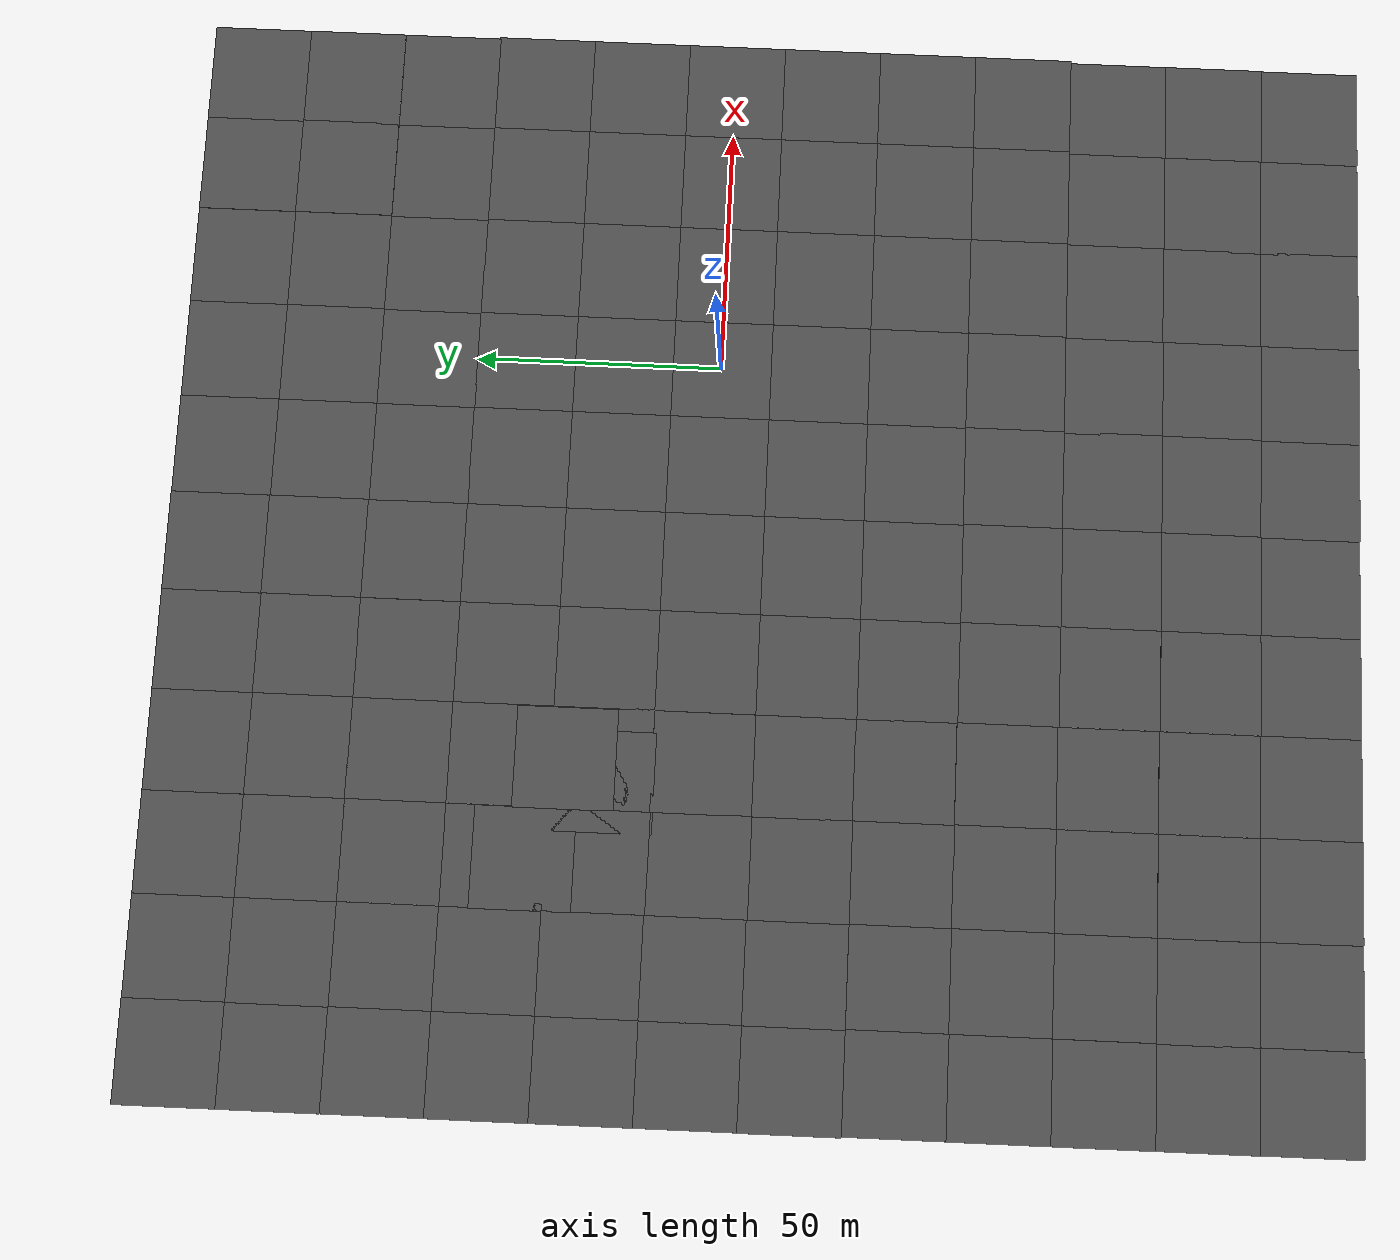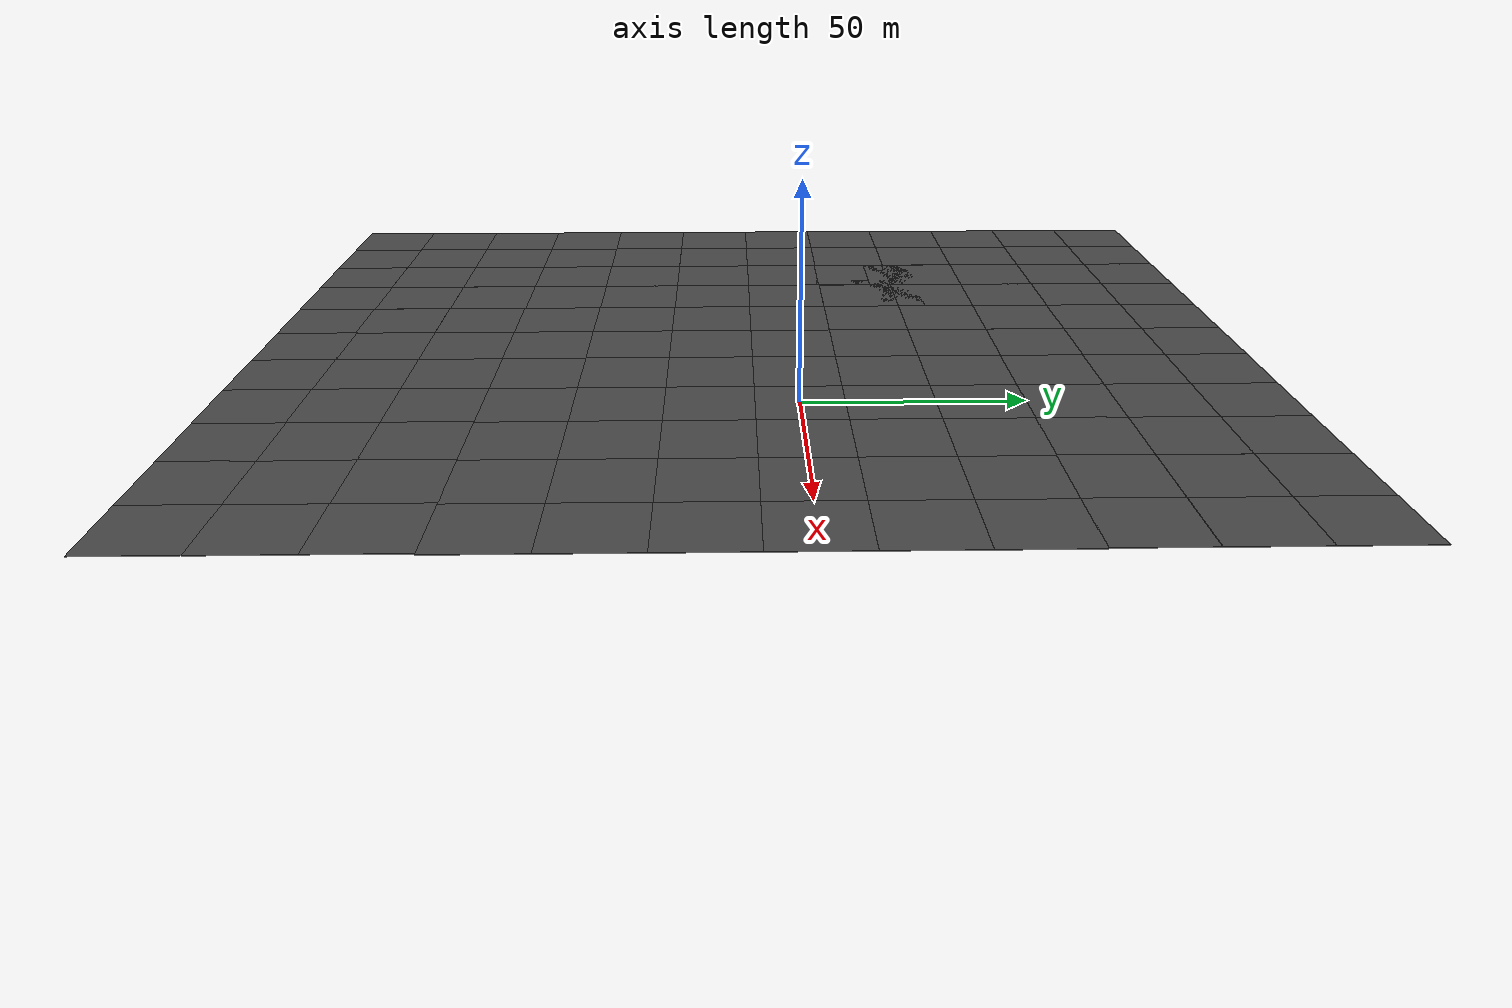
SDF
<sdf version="1.7">
 <world name="default">
  <light name="sun" type="directional">
   <pose>0 0 10 0 -0 0</pose>
   <diffuse>0.8 0.8 0.8 1</diffuse>
   <specular>0.2 0.2 0.2 1</specular>
   <attenuation>
    <range>1000</range>
    <constant>0.9</constant>
    <linear>0.01</linear>
    <quadratic>0.001</quadratic>
   </attenuation>
   <direction>-0.5 0.1 -0.9</direction>
   <spot><inner_angle>0</inner_angle><outer_angle>0</outer_angle><falloff>0</falloff></spot>
  </light>
  <gravity>0 0 -9.8</gravity>
  <magnetic_field>6e-06 2.3e-05 -4.2e-05</magnetic_field>
  <atmosphere type="adiabatic"/>
  <physics name="default_physics" default="0" type="ode">
   <max_step_size>0.001</max_step_size>
   <real_time_factor>1</real_time_factor>
   <real_time_update_rate>1000</real_time_update_rate>
  </physics>
  <scene><ambient>0.4 0.4 0.4 1</ambient><background>0.7 0.7 0.7 1</background><shadows>1</shadows></scene>
  <spherical_coordinates>
   <surface_model>EARTH_WGS84</surface_model>
   <latitude_deg>0</latitude_deg>
   <longitude_deg>0</longitude_deg>
   <elevation>0</elevation>
   <heading_deg>0</heading_deg>
  </spherical_coordinates>
  <audio><device>default</device></audio>
  <model name="asphalt_plane">
   <static>1</static>
   <link name="link">
    <collision name="collision"><geometry><box><size>20 20 0.1</size></box></geometry></collision>
    <visual name="visual">
     <cast_shadows>0</cast_shadows>
     <geometry><box><size>20 20 0.1</size></box></geometry>
     <material>
      <script>
       <uri>model://asphalt_plane/materials/scripts</uri>
       <uri>model://asphalt_plane/materials/textures</uri>
       <name>vrc/asphalt</name>
      </script>
     </material>
    </visual>
   </link>
  </model>
  <model name="asphalt_plane_0">
   <static>1</static>
   <link name="link">
    <collision name="collision"><geometry><box><size>20 20 0.1</size></box></geometry></collision>
    <visual name="visual">
     <cast_shadows>0</cast_shadows>
     <geometry><box><size>20 20 0.1</size></box></geometry>
     <material>
      <script>
       <uri>model://asphalt_plane/materials/scripts</uri>
       <uri>model://asphalt_plane/materials/textures</uri>
       <name>vrc/asphalt</name>
      </script>
     </material>
    </visual>
   </link>
   <pose>-20 0 0 0 -0 0</pose>
  </model>
  <model name="asphalt_plane_1">
   <static>1</static>
   <link name="link">
    <collision name="collision"><geometry><box><size>20 20 0.1</size></box></geometry></collision>
    <visual name="visual">
     <cast_shadows>0</cast_shadows>
     <geometry><box><size>20 20 0.1</size></box></geometry>
     <material>
      <script>
       <uri>model://asphalt_plane/materials/scripts</uri>
       <uri>model://asphalt_plane/materials/textures</uri>
       <name>vrc/asphalt</name>
      </script>
     </material>
    </visual>
   </link>
   <pose>-40 0 0 0 -0 0</pose>
  </model>
  <model name="asphalt_plane_2">
   <static>1</static>
   <link name="link">
    <collision name="collision"><geometry><box><size>20 20 0.1</size></box></geometry></collision>
    <visual name="visual">
     <cast_shadows>0</cast_shadows>
     <geometry><box><size>20 20 0.1</size></box></geometry>
     <material>
      <script>
       <uri>model://asphalt_plane/materials/scripts</uri>
       <uri>model://asphalt_plane/materials/textures</uri>
       <name>vrc/asphalt</name>
      </script>
     </material>
    </visual>
   </link>
   <pose>20 0 0 0 -0 0</pose>
  </model>
  <model name="asphalt_plane_3">
   <static>1</static>
   <link name="link">
    <collision name="collision"><geometry><box><size>20 20 0.1</size></box></geometry></collision>
    <visual name="visual">
     <cast_shadows>0</cast_shadows>
     <geometry><box><size>20 20 0.1</size></box></geometry>
     <material>
      <script>
       <uri>model://asphalt_plane/materials/scripts</uri>
       <uri>model://asphalt_plane/materials/textures</uri>
       <name>vrc/asphalt</name>
      </script>
     </material>
    </visual>
   </link>
   <pose>40 0 0 0 -0 0</pose>
  </model>
  <model name="asphalt_plane_4">
   <static>1</static>
   <link name="link">
    <collision name="collision"><geometry><box><size>20 20 0.1</size></box></geometry></collision>
    <visual name="visual">
     <cast_shadows>0</cast_shadows>
     <geometry><box><size>20 20 0.1</size></box></geometry>
     <material>
      <script>
       <uri>model://asphalt_plane/materials/scripts</uri>
       <uri>model://asphalt_plane/materials/textures</uri>
       <name>vrc/asphalt</name>
      </script>
     </material>
    </visual>
   </link>
   <pose>0 -20 0 0 -0 0</pose>
  </model>
  <model name="asphalt_plane_5">
   <static>1</static>
   <link name="link">
    <collision name="collision"><geometry><box><size>20 20 0.1</size></box></geometry></collision>
    <visual name="visual">
     <cast_shadows>0</cast_shadows>
     <geometry><box><size>20 20 0.1</size></box></geometry>
     <material>
      <script>
       <uri>model://asphalt_plane/materials/scripts</uri>
       <uri>model://asphalt_plane/materials/textures</uri>
       <name>vrc/asphalt</name>
      </script>
     </material>
    </visual>
   </link>
   <pose>-20 -20 0 0 -0 0</pose>
  </model>
  <model name="asphalt_plane_6">
   <static>1</static>
   <link name="link">
    <collision name="collision"><geometry><box><size>20 20 0.1</size></box></geometry></collision>
    <visual name="visual">
     <cast_shadows>0</cast_shadows>
     <geometry><box><size>20 20 0.1</size></box></geometry>
     <material>
      <script>
       <uri>model://asphalt_plane/materials/scripts</uri>
       <uri>model://asphalt_plane/materials/textures</uri>
       <name>vrc/asphalt</name>
      </script>
     </material>
    </visual>
   </link>
   <pose>-40 -20 0 0 -0 0</pose>
  </model>
  <model name="asphalt_plane_7">
   <static>1</static>
   <link name="link">
    <collision name="collision"><geometry><box><size>20 20 0.1</size></box></geometry></collision>
    <visual name="visual">
     <cast_shadows>0</cast_shadows>
     <geometry><box><size>20 20 0.1</size></box></geometry>
     <material>
      <script>
       <uri>model://asphalt_plane/materials/scripts</uri>
       <uri>model://asphalt_plane/materials/textures</uri>
       <name>vrc/asphalt</name>
      </script>
     </material>
    </visual>
   </link>
   <pose>20 -20 0 0 -0 0</pose>
  </model>
  <model name="asphalt_plane_8">
   <static>1</static>
   <link name="link">
    <collision name="collision"><geometry><box><size>20 20 0.1</size></box></geometry></collision>
    <visual name="visual">
     <cast_shadows>0</cast_shadows>
     <geometry><box><size>20 20 0.1</size></box></geometry>
     <material>
      <script>
       <uri>model://asphalt_plane/materials/scripts</uri>
       <uri>model://asphalt_plane/materials/textures</uri>
       <name>vrc/asphalt</name>
      </script>
     </material>
    </visual>
   </link>
   <pose>40 -20 0 0 -0 0</pose>
  </model>
  <model name="asphalt_plane_9">
   <static>1</static>
   <link name="link">
    <collision name="collision"><geometry><box><size>20 20 0.1</size></box></geometry></collision>
    <visual name="visual">
     <cast_shadows>0</cast_shadows>
     <geometry><box><size>20 20 0.1</size></box></geometry>
     <material>
      <script>
       <uri>model://asphalt_plane/materials/scripts</uri>
       <uri>model://asphalt_plane/materials/textures</uri>
       <name>vrc/asphalt</name>
      </script>
     </material>
    </visual>
   </link>
   <pose>-40 20 0 0 -0 0</pose>
  </model>
  <model name="asphalt_plane_10">
   <static>1</static>
   <link name="link">
    <collision name="collision"><geometry><box><size>20 20 0.1</size></box></geometry></collision>
    <visual name="visual">
     <cast_shadows>0</cast_shadows>
     <geometry><box><size>20 20 0.1</size></box></geometry>
     <material>
      <script>
       <uri>model://asphalt_plane/materials/scripts</uri>
       <uri>model://asphalt_plane/materials/textures</uri>
       <name>vrc/asphalt</name>
      </script>
     </material>
    </visual>
   </link>
   <pose>-20 20 0 0 -0 0</pose>
  </model>
  <model name="asphalt_plane_11">
   <static>1</static>
   <link name="link">
    <collision name="collision"><geometry><box><size>20 20 0.1</size></box></geometry></collision>
    <visual name="visual">
     <cast_shadows>0</cast_shadows>
     <geometry><box><size>20 20 0.1</size></box></geometry>
     <material>
      <script>
       <uri>model://asphalt_plane/materials/scripts</uri>
       <uri>model://asphalt_plane/materials/textures</uri>
       <name>vrc/asphalt</name>
      </script>
     </material>
    </visual>
   </link>
   <pose>0 20 0 0 -0 0</pose>
  </model>
  <model name="asphalt_plane_12">
   <static>1</static>
   <link name="link">
    <collision name="collision"><geometry><box><size>20 20 0.1</size></box></geometry></collision>
    <visual name="visual">
     <cast_shadows>0</cast_shadows>
     <geometry><box><size>20 20 0.1</size></box></geometry>
     <material>
      <script>
       <uri>model://asphalt_plane/materials/scripts</uri>
       <uri>model://asphalt_plane/materials/textures</uri>
       <name>vrc/asphalt</name>
      </script>
     </material>
    </visual>
   </link>
   <pose>20 20 0 0 -0 0</pose>
  </model>
  <model name="asphalt_plane_13">
   <static>1</static>
   <link name="link">
    <collision name="collision"><geometry><box><size>20 20 0.1</size></box></geometry></collision>
    <visual name="visual">
     <cast_shadows>0</cast_shadows>
     <geometry><box><size>20 20 0.1</size></box></geometry>
     <material>
      <script>
       <uri>model://asphalt_plane/materials/scripts</uri>
       <uri>model://asphalt_plane/materials/textures</uri>
       <name>vrc/asphalt</name>
      </script>
     </material>
    </visual>
   </link>
   <pose>40 20 0 0 -0 0</pose>
  </model>
  <model name="asphalt_plane_14">
   <static>1</static>
   <link name="link">
    <collision name="collision"><geometry><box><size>20 20 0.1</size></box></geometry></collision>
    <visual name="visual">
     <cast_shadows>0</cast_shadows>
     <geometry><box><size>20 20 0.1</size></box></geometry>
     <material>
      <script>
       <uri>model://asphalt_plane/materials/scripts</uri>
       <uri>model://asphalt_plane/materials/textures</uri>
       <name>vrc/asphalt</name>
      </script>
     </material>
    </visual>
   </link>
   <pose>60 0 0 0 -0 0</pose>
  </model>
  <model name="asphalt_plane_15">
   <static>1</static>
   <link name="link">
    <collision name="collision"><geometry><box><size>20 20 0.1</size></box></geometry></collision>
    <visual name="visual">
     <cast_shadows>0</cast_shadows>
     <geometry><box><size>20 20 0.1</size></box></geometry>
     <material>
      <script>
       <uri>model://asphalt_plane/materials/scripts</uri>
       <uri>model://asphalt_plane/materials/textures</uri>
       <name>vrc/asphalt</name>
      </script>
     </material>
    </visual>
   </link>
   <pose>60 20 0 0 -0 0</pose>
  </model>
  <model name="asphalt_plane_16">
   <static>1</static>
   <link name="link">
    <collision name="collision"><geometry><box><size>20 20 0.1</size></box></geometry></collision>
    <visual name="visual">
     <cast_shadows>0</cast_shadows>
     <geometry><box><size>20 20 0.1</size></box></geometry>
     <material>
      <script>
       <uri>model://asphalt_plane/materials/scripts</uri>
       <uri>model://asphalt_plane/materials/textures</uri>
       <name>vrc/asphalt</name>
      </script>
     </material>
    </visual>
   </link>
   <pose>60 -20 0 0 -0 0</pose>
  </model>
  <model name="asphalt_plane_17">
   <static>1</static>
   <link name="link">
    <collision name="collision"><geometry><box><size>20 20 0.1</size></box></geometry></collision>
    <visual name="visual">
     <cast_shadows>0</cast_shadows>
     <geometry><box><size>20 20 0.1</size></box></geometry>
     <material>
      <script>
       <uri>model://asphalt_plane/materials/scripts</uri>
       <uri>model://asphalt_plane/materials/textures</uri>
       <name>vrc/asphalt</name>
      </script>
     </material>
    </visual>
   </link>
   <pose>40 -40 0 0 -0 0</pose>
  </model>
  <model name="asphalt_plane_18">
   <static>1</static>
   <link name="link">
    <collision name="collision"><geometry><box><size>20 20 0.1</size></box></geometry></collision>
    <visual name="visual">
     <cast_shadows>0</cast_shadows>
     <geometry><box><size>20 20 0.1</size></box></geometry>
     <material>
      <script>
       <uri>model://asphalt_plane/materials/scripts</uri>
       <uri>model://asphalt_plane/materials/textures</uri>
       <name>vrc/asphalt</name>
      </script>
     </material>
    </visual>
   </link>
   <pose>60 -40 0 0 -0 0</pose>
  </model>
  <model name="asphalt_plane_19">
   <static>1</static>
   <link name="link">
    <collision name="collision"><geometry><box><size>20 20 0.1</size></box></geometry></collision>
    <visual name="visual">
     <cast_shadows>0</cast_shadows>
     <geometry><box><size>20 20 0.1</size></box></geometry>
     <material>
      <script>
       <uri>model://asphalt_plane/materials/scripts</uri>
       <uri>model://asphalt_plane/materials/textures</uri>
       <name>vrc/asphalt</name>
      </script>
     </material>
    </visual>
   </link>
   <pose>20 -40 0 0 -0 0</pose>
  </model>
  <model name="asphalt_plane_20">
   <static>1</static>
   <link name="link">
    <collision name="collision"><geometry><box><size>20 20 0.1</size></box></geometry></collision>
    <visual name="visual">
     <cast_shadows>0</cast_shadows>
     <geometry><box><size>20 20 0.1</size></box></geometry>
     <material>
      <script>
       <uri>model://asphalt_plane/materials/scripts</uri>
       <uri>model://asphalt_plane/materials/textures</uri>
       <name>vrc/asphalt</name>
      </script>
     </material>
    </visual>
   </link>
   <pose>0 -40 0 0 -0 0</pose>
  </model>
  <model name="asphalt_plane_21">
   <static>1</static>
   <link name="link">
    <collision name="collision"><geometry><box><size>20 20 0.1</size></box></geometry></collision>
    <visual name="visual">
     <cast_shadows>0</cast_shadows>
     <geometry><box><size>20 20 0.1</size></box></geometry>
     <material>
      <script>
       <uri>model://asphalt_plane/materials/scripts</uri>
       <uri>model://asphalt_plane/materials/textures</uri>
       <name>vrc/asphalt</name>
      </script>
     </material>
    </visual>
   </link>
   <pose>-20 -40 0 0 -0 0</pose>
  </model>
  <model name="asphalt_plane_22">
   <static>1</static>
   <link name="link">
    <collision name="collision"><geometry><box><size>20 20 0.1</size></box></geometry></collision>
    <visual name="visual">
     <cast_shadows>0</cast_shadows>
     <geometry><box><size>20 20 0.1</size></box></geometry>
     <material>
      <script>
       <uri>model://asphalt_plane/materials/scripts</uri>
       <uri>model://asphalt_plane/materials/textures</uri>
       <name>vrc/asphalt</name>
      </script>
     </material>
    </visual>
   </link>
   <pose>-40 -40 0 0 -0 0</pose>
  </model>
  <model name="asphalt_plane_23">
   <static>1</static>
   <link name="link">
    <collision name="collision"><geometry><box><size>20 20 0.1</size></box></geometry></collision>
    <visual name="visual">
     <cast_shadows>0</cast_shadows>
     <geometry><box><size>20 20 0.1</size></box></geometry>
     <material>
      <script>
       <uri>model://asphalt_plane/materials/scripts</uri>
       <uri>model://asphalt_plane/materials/textures</uri>
       <name>vrc/asphalt</name>
      </script>
     </material>
    </visual>
   </link>
   <pose>-60 -40 0 0 -0 0</pose>
  </model>
  <model name="asphalt_plane_24">
   <static>1</static>
   <link name="link">
    <collision name="collision"><geometry><box><size>20 20 0.1</size></box></geometry></collision>
    <visual name="visual">
     <cast_shadows>0</cast_shadows>
     <geometry><box><size>20 20 0.1</size></box></geometry>
     <material>
      <script>
       <uri>model://asphalt_plane/materials/scripts</uri>
       <uri>model://asphalt_plane/materials/textures</uri>
       <name>vrc/asphalt</name>
      </script>
     </material>
    </visual>
   </link>
   <pose>-60 -20 0 0 -0 0</pose>
  </model>
  <model name="asphalt_plane_25">
   <static>1</static>
   <link name="link">
    <collision name="collision"><geometry><box><size>20 20 0.1</size></box></geometry></collision>
    <visual name="visual">
     <cast_shadows>0</cast_shadows>
     <geometry><box><size>20 20 0.1</size></box></geometry>
     <material>
      <script>
       <uri>model://asphalt_plane/materials/scripts</uri>
       <uri>model://asphalt_plane/materials/textures</uri>
       <name>vrc/asphalt</name>
      </script>
     </material>
    </visual>
   </link>
   <pose>-60 0 0 0 -0 0</pose>
  </model>
  <model name="asphalt_plane_26">
   <static>1</static>
   <link name="link">
    <collision name="collision"><geometry><box><size>20 20 0.1</size></box></geometry></collision>
    <visual name="visual">
     <cast_shadows>0</cast_shadows>
     <geometry><box><size>20 20 0.1</size></box></geometry>
     <material>
      <script>
       <uri>model://asphalt_plane/materials/scripts</uri>
       <uri>model://asphalt_plane/materials/textures</uri>
       <name>vrc/asphalt</name>
      </script>
     </material>
    </visual>
   </link>
   <pose>-60 20 0 0 -0 0</pose>
  </model>
  <model name="asphalt_plane_27">
   <static>1</static>
   <link name="link">
    <collision name="collision"><geometry><box><size>20 20 0.1</size></box></geometry></collision>
    <visual name="visual">
     <cast_shadows>0</cast_shadows>
     <geometry><box><size>20 20 0.1</size></box></geometry>
     <material>
      <script>
       <uri>model://asphalt_plane/materials/scripts</uri>
       <uri>model://asphalt_plane/materials/textures</uri>
       <name>vrc/asphalt</name>
      </script>
     </material>
    </visual>
   </link>
   <pose>-60 40 0 0 -0 0</pose>
  </model>
  <model name="asphalt_plane_28">
   <static>1</static>
   <link name="link">
    <collision name="collision"><geometry><box><size>20 20 0.1</size></box></geometry></collision>
    <visual name="visual">
     <cast_shadows>0</cast_shadows>
     <geometry><box><size>20 20 0.1</size></box></geometry>
     <material>
      <script>
       <uri>model://asphalt_plane/materials/scripts</uri>
       <uri>model://asphalt_plane/materials/textures</uri>
       <name>vrc/asphalt</name>
      </script>
     </material>
    </visual>
   </link>
   <pose>-40 40 0 0 -0 0</pose>
  </model>
  <model name="asphalt_plane_29">
   <static>1</static>
   <link name="link">
    <collision name="collision"><geometry><box><size>20 20 0.1</size></box></geometry></collision>
    <visual name="visual">
     <cast_shadows>0</cast_shadows>
     <geometry><box><size>20 20 0.1</size></box></geometry>
     <material>
      <script>
       <uri>model://asphalt_plane/materials/scripts</uri>
       <uri>model://asphalt_plane/materials/textures</uri>
       <name>vrc/asphalt</name>
      </script>
     </material>
    </visual>
   </link>
   <pose>-20 40 0 0 -0 0</pose>
  </model>
  <model name="asphalt_plane_30">
   <static>1</static>
   <link name="link">
    <collision name="collision"><geometry><box><size>20 20 0.1</size></box></geometry></collision>
    <visual name="visual">
     <cast_shadows>0</cast_shadows>
     <geometry><box><size>20 20 0.1</size></box></geometry>
     <material>
      <script>
       <uri>model://asphalt_plane/materials/scripts</uri>
       <uri>model://asphalt_plane/materials/textures</uri>
       <name>vrc/asphalt</name>
      </script>
     </material>
    </visual>
   </link>
   <pose>0 40 0 0 -0 0</pose>
  </model>
  <model name="asphalt_plane_31">
   <static>1</static>
   <link name="link">
    <collision name="collision"><geometry><box><size>20 20 0.1</size></box></geometry></collision>
    <visual name="visual">
     <cast_shadows>0</cast_shadows>
     <geometry><box><size>20 20 0.1</size></box></geometry>
     <material>
      <script>
       <uri>model://asphalt_plane/materials/scripts</uri>
       <uri>model://asphalt_plane/materials/textures</uri>
       <name>vrc/asphalt</name>
      </script>
     </material>
    </visual>
   </link>
   <pose>20 40 0 0 -0 0</pose>
  </model>
  <model name="asphalt_plane_32">
   <static>1</static>
   <link name="link">
    <collision name="collision"><geometry><box><size>20 20 0.1</size></box></geometry></collision>
    <visual name="visual">
     <cast_shadows>0</cast_shadows>
     <geometry><box><size>20 20 0.1</size></box></geometry>
     <material>
      <script>
       <uri>model://asphalt_plane/materials/scripts</uri>
       <uri>model://asphalt_plane/materials/textures</uri>
       <name>vrc/asphalt</name>
      </script>
     </material>
    </visual>
   </link>
   <pose>40 40 0 0 -0 0</pose>
  </model>
  <model name="asphalt_plane_33">
   <static>1</static>
   <link name="link">
    <collision name="collision"><geometry><box><size>20 20 0.1</size></box></geometry></collision>
    <visual name="visual">
     <cast_shadows>0</cast_shadows>
     <geometry><box><size>20 20 0.1</size></box></geometry>
     <material>
      <script>
       <uri>model://asphalt_plane/materials/scripts</uri>
       <uri>model://asphalt_plane/materials/textures</uri>
       <name>vrc/asphalt</name>
      </script>
     </material>
    </visual>
   </link>
   <pose>60 40 0 0 -0 0</pose>
  </model>
  <model name="asphalt_plane_18_clone">
   <static>1</static>
   <link name="link">
    <collision name="collision"><geometry><box><size>20 20 0.1</size></box></geometry></collision>
    <visual name="visual">
     <cast_shadows>0</cast_shadows>
     <geometry><box><size>20 20 0.1</size></box></geometry>
     <material>
      <script>
       <uri>model://asphalt_plane/materials/scripts</uri>
       <uri>model://asphalt_plane/materials/textures</uri>
       <name>vrc/asphalt</name>
      </script>
     </material>
    </visual>
   </link>
   <pose>59.9964 -59.9875 0 0 -0 0</pose>
  </model>
  <model name="asphalt_plane_23_clone">
   <static>1</static>
   <link name="link">
    <collision name="collision"><geometry><box><size>20 20 0.1</size></box></geometry></collision>
    <visual name="visual">
     <cast_shadows>0</cast_shadows>
     <geometry><box><size>20 20 0.1</size></box></geometry>
     <material>
      <script>
       <uri>model://asphalt_plane/materials/scripts</uri>
       <uri>model://asphalt_plane/materials/textures</uri>
       <name>vrc/asphalt</name>
      </script>
     </material>
    </visual>
   </link>
   <pose>40.0178 -59.9822 0 0 -0 0</pose>
  </model>
  <model name="asphalt_plane_23_clone_0">
   <static>1</static>
   <link name="link">
    <collision name="collision"><geometry><box><size>20 20 0.1</size></box></geometry></collision>
    <visual name="visual">
     <cast_shadows>0</cast_shadows>
     <geometry><box><size>20 20 0.1</size></box></geometry>
     <material>
      <script>
       <uri>model://asphalt_plane/materials/scripts</uri>
       <uri>model://asphalt_plane/materials/textures</uri>
       <name>vrc/asphalt</name>
      </script>
     </material>
    </visual>
   </link>
   <pose>20.0657 -59.997 0 0 -0 0</pose>
  </model>
  <model name="asphalt_plane_27_clone">
   <static>1</static>
   <link name="link">
    <collision name="collision"><geometry><box><size>20 20 0.1</size></box></geometry></collision>
    <visual name="visual">
     <cast_shadows>0</cast_shadows>
     <geometry><box><size>20 20 0.1</size></box></geometry>
     <material>
      <script>
       <uri>model://asphalt_plane/materials/scripts</uri>
       <uri>model://asphalt_plane/materials/textures</uri>
       <name>vrc/asphalt</name>
      </script>
     </material>
    </visual>
   </link>
   <pose>-60.0136 59.9859 0 0 -0 0</pose>
  </model>
  <model name="asphalt_plane_27_clone_0">
   <static>1</static>
   <link name="link">
    <collision name="collision"><geometry><box><size>20 20 0.1</size></box></geometry></collision>
    <visual name="visual">
     <cast_shadows>0</cast_shadows>
     <geometry><box><size>20 20 0.1</size></box></geometry>
     <material>
      <script>
       <uri>model://asphalt_plane/materials/scripts</uri>
       <uri>model://asphalt_plane/materials/textures</uri>
       <name>vrc/asphalt</name>
      </script>
     </material>
    </visual>
   </link>
   <pose>-39.9999 59.992 0 0 -0 0</pose>
  </model>
  <model name="asphalt_plane_27_clone_clone">
   <static>1</static>
   <link name="link">
    <collision name="collision"><geometry><box><size>20 20 0.1</size></box></geometry></collision>
    <visual name="visual">
     <cast_shadows>0</cast_shadows>
     <geometry><box><size>20 20 0.1</size></box></geometry>
     <material>
      <script>
       <uri>model://asphalt_plane/materials/scripts</uri>
       <uri>model://asphalt_plane/materials/textures</uri>
       <name>vrc/asphalt</name>
      </script>
     </material>
    </visual>
   </link>
   <pose>-39.9881 79.9797 0 0 -0 0</pose>
  </model>
  <model name="asphalt_plane_27_clone_1">
   <static>1</static>
   <link name="link">
    <collision name="collision"><geometry><box><size>20 20 0.1</size></box></geometry></collision>
    <visual name="visual">
     <cast_shadows>0</cast_shadows>
     <geometry><box><size>20 20 0.1</size></box></geometry>
     <material>
      <script>
       <uri>model://asphalt_plane/materials/scripts</uri>
       <uri>model://asphalt_plane/materials/textures</uri>
       <name>vrc/asphalt</name>
      </script>
     </material>
    </visual>
   </link>
   <pose>-59.9581 79.901 0 0 -0 0</pose>
  </model>
  <model name="asphalt_plane_27_clone_2">
   <static>1</static>
   <link name="link">
    <collision name="collision"><geometry><box><size>20 20 0.1</size></box></geometry></collision>
    <visual name="visual">
     <cast_shadows>0</cast_shadows>
     <geometry><box><size>20 20 0.1</size></box></geometry>
     <material>
      <script>
       <uri>model://asphalt_plane/materials/scripts</uri>
       <uri>model://asphalt_plane/materials/textures</uri>
       <name>vrc/asphalt</name>
      </script>
     </material>
    </visual>
   </link>
   <pose>-79.9559 79.9056 0 0 -0 0</pose>
  </model>
  <model name="asphalt_plane_27_clone_1_clone">
   <static>1</static>
   <link name="link">
    <collision name="collision"><geometry><box><size>20 20 0.1</size></box></geometry></collision>
    <visual name="visual">
     <cast_shadows>0</cast_shadows>
     <geometry><box><size>20 20 0.1</size></box></geometry>
     <material>
      <script>
       <uri>model://asphalt_plane/materials/scripts</uri>
       <uri>model://asphalt_plane/materials/textures</uri>
       <name>vrc/asphalt</name>
      </script>
     </material>
    </visual>
   </link>
   <pose>-79.9276 60.0054 0 0 -0 0</pose>
  </model>
  <model name="asphalt_plane_27_clone_1_clone_0">
   <static>1</static>
   <link name="link">
    <collision name="collision"><geometry><box><size>20 20 0.1</size></box></geometry></collision>
    <visual name="visual">
     <cast_shadows>0</cast_shadows>
     <geometry><box><size>20 20 0.1</size></box></geometry>
     <material>
      <script>
       <uri>model://asphalt_plane/materials/scripts</uri>
       <uri>model://asphalt_plane/materials/textures</uri>
       <name>vrc/asphalt</name>
      </script>
     </material>
    </visual>
   </link>
   <pose>-99.9415 79.9063 0 0 -0 0</pose>
  </model>
  <model name="asphalt_plane_27_clone_1_clone_1">
   <static>1</static>
   <link name="link">
    <collision name="collision"><geometry><box><size>20 20 0.1</size></box></geometry></collision>
    <visual name="visual">
     <cast_shadows>0</cast_shadows>
     <geometry><box><size>20 20 0.1</size></box></geometry>
     <material>
      <script>
       <uri>model://asphalt_plane/materials/scripts</uri>
       <uri>model://asphalt_plane/materials/textures</uri>
       <name>vrc/asphalt</name>
      </script>
     </material>
    </visual>
   </link>
   <pose>-99.8424 59.9488 0 0 -0 0</pose>
  </model>
  <model name="asphalt_plane_27_clone_clone_clone">
   <static>1</static>
   <link name="link">
    <collision name="collision"><geometry><box><size>20 20 0.1</size></box></geometry></collision>
    <visual name="visual">
     <cast_shadows>0</cast_shadows>
     <geometry><box><size>20 20 0.1</size></box></geometry>
     <material>
      <script>
       <uri>model://asphalt_plane/materials/scripts</uri>
       <uri>model://asphalt_plane/materials/textures</uri>
       <name>vrc/asphalt</name>
      </script>
     </material>
    </visual>
   </link>
   <pose>-119.935 79.8947 0 0 -0 0</pose>
  </model>
  <model name="asphalt_plane_27_clone_clone_clone_0">
   <static>1</static>
   <link name="link">
    <collision name="collision"><geometry><box><size>20 20 0.1</size></box></geometry></collision>
    <visual name="visual">
     <cast_shadows>0</cast_shadows>
     <geometry><box><size>20 20 0.1</size></box></geometry>
     <material>
      <script>
       <uri>model://asphalt_plane/materials/scripts</uri>
       <uri>model://asphalt_plane/materials/textures</uri>
       <name>vrc/asphalt</name>
      </script>
     </material>
    </visual>
   </link>
   <pose>-119.867 59.9806 0 0 -0 0</pose>
  </model>
  <model name="asphalt_plane_27_clone_1_clone_1_clone">
   <static>1</static>
   <link name="link">
    <collision name="collision"><geometry><box><size>20 20 0.1</size></box></geometry></collision>
    <visual name="visual">
     <cast_shadows>0</cast_shadows>
     <geometry><box><size>20 20 0.1</size></box></geometry>
     <material>
      <script>
       <uri>model://asphalt_plane/materials/scripts</uri>
       <uri>model://asphalt_plane/materials/textures</uri>
       <name>vrc/asphalt</name>
      </script>
     </material>
    </visual>
   </link>
   <pose>-139.858 79.9193 0 0 -0 0</pose>
  </model>
  <model name="asphalt_plane_27_clone_1_clone_1_clone_0">
   <static>1</static>
   <link name="link">
    <collision name="collision"><geometry><box><size>20 20 0.1</size></box></geometry></collision>
    <visual name="visual">
     <cast_shadows>0</cast_shadows>
     <geometry><box><size>20 20 0.1</size></box></geometry>
     <material>
      <script>
       <uri>model://asphalt_plane/materials/scripts</uri>
       <uri>model://asphalt_plane/materials/textures</uri>
       <name>vrc/asphalt</name>
      </script>
     </material>
    </visual>
   </link>
   <pose>-139.829 59.9334 0 0 -0 0</pose>
  </model>
  <model name="asphalt_plane_27_clone_1_clone_1_clone_clone">
   <static>1</static>
   <link name="link">
    <collision name="collision"><geometry><box><size>20 20 0.1</size></box></geometry></collision>
    <visual name="visual">
     <cast_shadows>0</cast_shadows>
     <geometry><box><size>20 20 0.1</size></box></geometry>
     <material>
      <script>
       <uri>model://asphalt_plane/materials/scripts</uri>
       <uri>model://asphalt_plane/materials/textures</uri>
       <name>vrc/asphalt</name>
      </script>
     </material>
    </visual>
   </link>
   <pose>-139.842 39.9853 0 0 -0 0</pose>
  </model>
  <model name="asphalt_plane_27_clone_1_clone_1_clone_clone_0">
   <static>1</static>
   <link name="link">
    <collision name="collision"><geometry><box><size>20 20 0.1</size></box></geometry></collision>
    <visual name="visual">
     <cast_shadows>0</cast_shadows>
     <geometry><box><size>20 20 0.1</size></box></geometry>
     <material>
      <script>
       <uri>model://asphalt_plane/materials/scripts</uri>
       <uri>model://asphalt_plane/materials/textures</uri>
       <name>vrc/asphalt</name>
      </script>
     </material>
    </visual>
   </link>
   <pose>-139.843 20.01 0 0 -0 0</pose>
  </model>
  <model name="asphalt_plane_27_clone_1_clone_1_clone_clone_1">
   <static>1</static>
   <link name="link">
    <collision name="collision"><geometry><box><size>20 20 0.1</size></box></geometry></collision>
    <visual name="visual">
     <cast_shadows>0</cast_shadows>
     <geometry><box><size>20 20 0.1</size></box></geometry>
     <material>
      <script>
       <uri>model://asphalt_plane/materials/scripts</uri>
       <uri>model://asphalt_plane/materials/textures</uri>
       <name>vrc/asphalt</name>
      </script>
     </material>
    </visual>
   </link>
   <pose>-139.832 0.068199 0 0 -0 0</pose>
  </model>
  <model name="asphalt_plane_27_clone_1_clone_1_clone_clone_2">
   <static>1</static>
   <link name="link">
    <collision name="collision"><geometry><box><size>20 20 0.1</size></box></geometry></collision>
    <visual name="visual">
     <cast_shadows>0</cast_shadows>
     <geometry><box><size>20 20 0.1</size></box></geometry>
     <material>
      <script>
       <uri>model://asphalt_plane/materials/scripts</uri>
       <uri>model://asphalt_plane/materials/textures</uri>
       <name>vrc/asphalt</name>
      </script>
     </material>
    </visual>
   </link>
   <pose>-139.882 -19.9008 0 0 -0 0</pose>
  </model>
  <model name="asphalt_plane_27_clone_1_clone_1_clone_clone_3">
   <static>1</static>
   <link name="link">
    <collision name="collision"><geometry><box><size>20 20 0.1</size></box></geometry></collision>
    <visual name="visual">
     <cast_shadows>0</cast_shadows>
     <geometry><box><size>20 20 0.1</size></box></geometry>
     <material>
      <script>
       <uri>model://asphalt_plane/materials/scripts</uri>
       <uri>model://asphalt_plane/materials/textures</uri>
       <name>vrc/asphalt</name>
      </script>
     </material>
    </visual>
   </link>
   <pose>-119.902 -19.9114 0 0 -0 0</pose>
  </model>
  <model name="asphalt_plane_27_clone_1_clone_1_clone_clone_4">
   <static>1</static>
   <link name="link">
    <collision name="collision"><geometry><box><size>20 20 0.1</size></box></geometry></collision>
    <visual name="visual">
     <cast_shadows>0</cast_shadows>
     <geometry><box><size>20 20 0.1</size></box></geometry>
     <material>
      <script>
       <uri>model://asphalt_plane/materials/scripts</uri>
       <uri>model://asphalt_plane/materials/textures</uri>
       <name>vrc/asphalt</name>
      </script>
     </material>
    </visual>
   </link>
   <pose>-99.9041 -19.9218 0 0 -0 0</pose>
  </model>
  <model name="asphalt_plane_27_clone_1_clone_1_clone_clone_5">
   <static>1</static>
   <link name="link">
    <collision name="collision"><geometry><box><size>20 20 0.1</size></box></geometry></collision>
    <visual name="visual">
     <cast_shadows>0</cast_shadows>
     <geometry><box><size>20 20 0.1</size></box></geometry>
     <material>
      <script>
       <uri>model://asphalt_plane/materials/scripts</uri>
       <uri>model://asphalt_plane/materials/textures</uri>
       <name>vrc/asphalt</name>
      </script>
     </material>
    </visual>
   </link>
   <pose>-119.886 0.053935 0 0 -0 0</pose>
  </model>
  <model name="asphalt_plane_27_clone_1_clone_1_clone_clone_6">
   <static>1</static>
   <link name="link">
    <collision name="collision"><geometry><box><size>20 20 0.1</size></box></geometry></collision>
    <visual name="visual">
     <cast_shadows>0</cast_shadows>
     <geometry><box><size>20 20 0.1</size></box></geometry>
     <material>
      <script>
       <uri>model://asphalt_plane/materials/scripts</uri>
       <uri>model://asphalt_plane/materials/textures</uri>
       <name>vrc/asphalt</name>
      </script>
     </material>
    </visual>
   </link>
   <pose>-99.902 -0.148769 0 0 -0 0</pose>
  </model>
  <model name="asphalt_plane_27_clone_1_clone_1_clone_clone_7">
   <static>1</static>
   <link name="link">
    <collision name="collision"><geometry><box><size>20 20 0.1</size></box></geometry></collision>
    <visual name="visual">
     <cast_shadows>0</cast_shadows>
     <geometry><box><size>20 20 0.1</size></box></geometry>
     <material>
      <script>
       <uri>model://asphalt_plane/materials/scripts</uri>
       <uri>model://asphalt_plane/materials/textures</uri>
       <name>vrc/asphalt</name>
      </script>
     </material>
    </visual>
   </link>
   <pose>-79.9947 -19.9094 0 0 -0 0</pose>
  </model>
  <model name="asphalt_plane_27_clone_1_clone_1_clone_clone_8">
   <static>1</static>
   <link name="link">
    <collision name="collision"><geometry><box><size>20 20 0.1</size></box></geometry></collision>
    <visual name="visual">
     <cast_shadows>0</cast_shadows>
     <geometry><box><size>20 20 0.1</size></box></geometry>
     <material>
      <script>
       <uri>model://asphalt_plane/materials/scripts</uri>
       <uri>model://asphalt_plane/materials/textures</uri>
       <name>vrc/asphalt</name>
      </script>
     </material>
    </visual>
   </link>
   <pose>-80.0055 -0.037354 0 0 -0 0</pose>
  </model>
  <model name="asphalt_plane_27_clone_1_clone_1_clone_clone_9">
   <static>1</static>
   <link name="link">
    <collision name="collision"><geometry><box><size>20 20 0.1</size></box></geometry></collision>
    <visual name="visual">
     <cast_shadows>0</cast_shadows>
     <geometry><box><size>20 20 0.1</size></box></geometry>
     <material>
      <script>
       <uri>model://asphalt_plane/materials/scripts</uri>
       <uri>model://asphalt_plane/materials/textures</uri>
       <name>vrc/asphalt</name>
      </script>
     </material>
    </visual>
   </link>
   <pose>-79.8891 -39.8116 0 0 -0 0</pose>
  </model>
  <model name="asphalt_plane_27_clone_1_clone_1_clone_clone_10">
   <static>1</static>
   <link name="link">
    <collision name="collision"><geometry><box><size>20 20 0.1</size></box></geometry></collision>
    <visual name="visual">
     <cast_shadows>0</cast_shadows>
     <geometry><box><size>20 20 0.1</size></box></geometry>
     <material>
      <script>
       <uri>model://asphalt_plane/materials/scripts</uri>
       <uri>model://asphalt_plane/materials/textures</uri>
       <name>vrc/asphalt</name>
      </script>
     </material>
    </visual>
   </link>
   <pose>-99.7977 -39.9115 0 0 -0 0</pose>
  </model>
  <model name="asphalt_plane_27_clone_1_clone_1_clone_clone_11">
   <static>1</static>
   <link name="link">
    <collision name="collision"><geometry><box><size>20 20 0.1</size></box></geometry></collision>
    <visual name="visual">
     <cast_shadows>0</cast_shadows>
     <geometry><box><size>20 20 0.1</size></box></geometry>
     <material>
      <script>
       <uri>model://asphalt_plane/materials/scripts</uri>
       <uri>model://asphalt_plane/materials/textures</uri>
       <name>vrc/asphalt</name>
      </script>
     </material>
    </visual>
   </link>
   <pose>-119.778 -39.9212 0 0 -0 0</pose>
  </model>
  <model name="asphalt_plane_27_clone_1_clone_1_clone_clone_12">
   <static>1</static>
   <link name="link">
    <collision name="collision"><geometry><box><size>20 20 0.1</size></box></geometry></collision>
    <visual name="visual">
     <cast_shadows>0</cast_shadows>
     <geometry><box><size>20 20 0.1</size></box></geometry>
     <material>
      <script>
       <uri>model://asphalt_plane/materials/scripts</uri>
       <uri>model://asphalt_plane/materials/textures</uri>
       <name>vrc/asphalt</name>
      </script>
     </material>
    </visual>
   </link>
   <pose>-139.697 -39.9019 0 0 -0 0</pose>
  </model>
  <model name="asphalt_plane_27_clone_1_clone_1_clone_clone_2_clone">
   <static>1</static>
   <link name="link">
    <collision name="collision"><geometry><box><size>20 20 0.1</size></box></geometry></collision>
    <visual name="visual">
     <cast_shadows>0</cast_shadows>
     <geometry><box><size>20 20 0.1</size></box></geometry>
     <material>
      <script>
       <uri>model://asphalt_plane/materials/scripts</uri>
       <uri>model://asphalt_plane/materials/textures</uri>
       <name>vrc/asphalt</name>
      </script>
     </material>
    </visual>
   </link>
   <pose>0.157661 -59.9598 0 0 -0 0</pose>
  </model>
  <model name="asphalt_plane_27_clone_1_clone_1_clone_clone_2_clone_0">
   <static>1</static>
   <link name="link">
    <collision name="collision"><geometry><box><size>20 20 0.1</size></box></geometry></collision>
    <visual name="visual">
     <cast_shadows>0</cast_shadows>
     <geometry><box><size>20 20 0.1</size></box></geometry>
     <material>
      <script>
       <uri>model://asphalt_plane/materials/scripts</uri>
       <uri>model://asphalt_plane/materials/textures</uri>
       <name>vrc/asphalt</name>
      </script>
     </material>
    </visual>
   </link>
   <pose>-19.8396 -59.9622 0 0 -0 0</pose>
  </model>
  <model name="asphalt_plane_27_clone_1_clone_1_clone_clone_2_clone_1">
   <static>1</static>
   <link name="link">
    <collision name="collision"><geometry><box><size>20 20 0.1</size></box></geometry></collision>
    <visual name="visual">
     <cast_shadows>0</cast_shadows>
     <geometry><box><size>20 20 0.1</size></box></geometry>
     <material>
      <script>
       <uri>model://asphalt_plane/materials/scripts</uri>
       <uri>model://asphalt_plane/materials/textures</uri>
       <name>vrc/asphalt</name>
      </script>
     </material>
    </visual>
   </link>
   <pose>-39.7931 -59.9957 0 0 -0 0</pose>
  </model>
  <model name="asphalt_plane_27_clone_1_clone_1_clone_clone_2_clone_2">
   <static>1</static>
   <link name="link">
    <collision name="collision"><geometry><box><size>20 20 0.1</size></box></geometry></collision>
    <visual name="visual">
     <cast_shadows>0</cast_shadows>
     <geometry><box><size>20 20 0.1</size></box></geometry>
     <material>
      <script>
       <uri>model://asphalt_plane/materials/scripts</uri>
       <uri>model://asphalt_plane/materials/textures</uri>
       <name>vrc/asphalt</name>
      </script>
     </material>
    </visual>
   </link>
   <pose>-59.7618 -59.9573 0 0 -0 0</pose>
  </model>
  <model name="asphalt_plane_27_clone_1_clone_1_clone_clone_2_clone_3">
   <static>1</static>
   <link name="link">
    <collision name="collision"><geometry><box><size>20 20 0.1</size></box></geometry></collision>
    <visual name="visual">
     <cast_shadows>0</cast_shadows>
     <geometry><box><size>20 20 0.1</size></box></geometry>
     <material>
      <script>
       <uri>model://asphalt_plane/materials/scripts</uri>
       <uri>model://asphalt_plane/materials/textures</uri>
       <name>vrc/asphalt</name>
      </script>
     </material>
    </visual>
   </link>
   <pose>-59.7385 -79.9238 0 0 -0 0</pose>
  </model>
  <model name="asphalt_plane_27_clone_1_clone_1_clone_clone_2_clone_4">
   <static>1</static>
   <link name="link">
    <collision name="collision"><geometry><box><size>20 20 0.1</size></box></geometry></collision>
    <visual name="visual">
     <cast_shadows>0</cast_shadows>
     <geometry><box><size>20 20 0.1</size></box></geometry>
     <material>
      <script>
       <uri>model://asphalt_plane/materials/scripts</uri>
       <uri>model://asphalt_plane/materials/textures</uri>
       <name>vrc/asphalt</name>
      </script>
     </material>
    </visual>
   </link>
   <pose>-39.7511 -79.9418 0 0 -0 0</pose>
  </model>
  <model name="asphalt_plane_27_clone_1_clone_1_clone_clone_2_clone_5">
   <static>1</static>
   <link name="link">
    <collision name="collision"><geometry><box><size>20 20 0.1</size></box></geometry></collision>
    <visual name="visual">
     <cast_shadows>0</cast_shadows>
     <geometry><box><size>20 20 0.1</size></box></geometry>
     <material>
      <script>
       <uri>model://asphalt_plane/materials/scripts</uri>
       <uri>model://asphalt_plane/materials/textures</uri>
       <name>vrc/asphalt</name>
      </script>
     </material>
    </visual>
   </link>
   <pose>-19.798 -79.9135 0 0 -0 0</pose>
  </model>
  <model name="asphalt_plane_27_clone_1_clone_1_clone_clone_2_clone_6">
   <static>1</static>
   <link name="link">
    <collision name="collision"><geometry><box><size>20 20 0.1</size></box></geometry></collision>
    <visual name="visual">
     <cast_shadows>0</cast_shadows>
     <geometry><box><size>20 20 0.1</size></box></geometry>
     <material>
      <script>
       <uri>model://asphalt_plane/materials/scripts</uri>
       <uri>model://asphalt_plane/materials/textures</uri>
       <name>vrc/asphalt</name>
      </script>
     </material>
    </visual>
   </link>
   <pose>-0.179278 -79.9081 0 0 -0 0</pose>
  </model>
  <model name="asphalt_plane_27_clone_1_clone_1_clone_clone_2_clone_7">
   <static>1</static>
   <link name="link">
    <collision name="collision"><geometry><box><size>20 20 0.1</size></box></geometry></collision>
    <visual name="visual">
     <cast_shadows>0</cast_shadows>
     <geometry><box><size>20 20 0.1</size></box></geometry>
     <material>
      <script>
       <uri>model://asphalt_plane/materials/scripts</uri>
       <uri>model://asphalt_plane/materials/textures</uri>
       <name>vrc/asphalt</name>
      </script>
     </material>
    </visual>
   </link>
   <pose>-59.7435 -99.9572 0 0 -0 0</pose>
  </model>
  <model name="asphalt_plane_27_clone_1_clone_1_clone_clone_2_clone_8">
   <static>1</static>
   <link name="link">
    <collision name="collision"><geometry><box><size>20 20 0.1</size></box></geometry></collision>
    <visual name="visual">
     <cast_shadows>0</cast_shadows>
     <geometry><box><size>20 20 0.1</size></box></geometry>
     <material>
      <script>
       <uri>model://asphalt_plane/materials/scripts</uri>
       <uri>model://asphalt_plane/materials/textures</uri>
       <name>vrc/asphalt</name>
      </script>
     </material>
    </visual>
   </link>
   <pose>-39.7903 -99.9163 0 0 -0 0</pose>
  </model>
  <model name="asphalt_plane_27_clone_1_clone_1_clone_clone_2_clone_9">
   <static>1</static>
   <link name="link">
    <collision name="collision"><geometry><box><size>20 20 0.1</size></box></geometry></collision>
    <visual name="visual">
     <cast_shadows>0</cast_shadows>
     <geometry><box><size>20 20 0.1</size></box></geometry>
     <material>
      <script>
       <uri>model://asphalt_plane/materials/scripts</uri>
       <uri>model://asphalt_plane/materials/textures</uri>
       <name>vrc/asphalt</name>
      </script>
     </material>
    </visual>
   </link>
   <pose>-19.8411 -99.8531 0 0 -0 0</pose>
  </model>
  <model name="asphalt_plane_27_clone_1_clone_1_clone_clone_2_clone_10">
   <static>1</static>
   <link name="link">
    <collision name="collision"><geometry><box><size>20 20 0.1</size></box></geometry></collision>
    <visual name="visual">
     <cast_shadows>0</cast_shadows>
     <geometry><box><size>20 20 0.1</size></box></geometry>
     <material>
      <script>
       <uri>model://asphalt_plane/materials/scripts</uri>
       <uri>model://asphalt_plane/materials/textures</uri>
       <name>vrc/asphalt</name>
      </script>
     </material>
    </visual>
   </link>
   <pose>-0.180116 -99.8911 0 0 -0 0</pose>
  </model>
  <model name="asphalt_plane_27_clone_1_clone_1_clone_clone_2_clone_8_clone">
   <static>1</static>
   <link name="link">
    <collision name="collision"><geometry><box><size>20 20 0.1</size></box></geometry></collision>
    <visual name="visual">
     <cast_shadows>0</cast_shadows>
     <geometry><box><size>20 20 0.1</size></box></geometry>
     <material>
      <script>
       <uri>model://asphalt_plane/materials/scripts</uri>
       <uri>model://asphalt_plane/materials/textures</uri>
       <name>vrc/asphalt</name>
      </script>
     </material>
    </visual>
   </link>
   <pose>-0.167839 -119.783 0 0 -0 0</pose>
  </model>
  <model name="asphalt_plane_27_clone_1_clone_1_clone_clone_2_clone_8_clone_0">
   <static>1</static>
   <link name="link">
    <collision name="collision"><geometry><box><size>20 20 0.1</size></box></geometry></collision>
    <visual name="visual">
     <cast_shadows>0</cast_shadows>
     <geometry><box><size>20 20 0.1</size></box></geometry>
     <material>
      <script>
       <uri>model://asphalt_plane/materials/scripts</uri>
       <uri>model://asphalt_plane/materials/textures</uri>
       <name>vrc/asphalt</name>
      </script>
     </material>
    </visual>
   </link>
   <pose>-20.0015 -119.752 0 0 -0 0</pose>
  </model>
  <model name="asphalt_plane_27_clone_1_clone_1_clone_clone_2_clone_8_clone_1">
   <static>1</static>
   <link name="link">
    <collision name="collision"><geometry><box><size>20 20 0.1</size></box></geometry></collision>
    <visual name="visual">
     <cast_shadows>0</cast_shadows>
     <geometry><box><size>20 20 0.1</size></box></geometry>
     <material>
      <script>
       <uri>model://asphalt_plane/materials/scripts</uri>
       <uri>model://asphalt_plane/materials/textures</uri>
       <name>vrc/asphalt</name>
      </script>
     </material>
    </visual>
   </link>
   <pose>19.8184 -119.711 0 0 -0 0</pose>
  </model>
  <model name="asphalt_plane_27_clone_1_clone_1_clone_clone_2_clone_8_clone_2">
   <static>1</static>
   <link name="link">
    <collision name="collision"><geometry><box><size>20 20 0.1</size></box></geometry></collision>
    <visual name="visual">
     <cast_shadows>0</cast_shadows>
     <geometry><box><size>20 20 0.1</size></box></geometry>
     <material>
      <script>
       <uri>model://asphalt_plane/materials/scripts</uri>
       <uri>model://asphalt_plane/materials/textures</uri>
       <name>vrc/asphalt</name>
      </script>
     </material>
    </visual>
   </link>
   <pose>39.4937 -119.729 0 0 -0 0</pose>
  </model>
  <model name="asphalt_plane_27_clone_1_clone_1_clone_clone_2_clone_8_clone_3">
   <static>1</static>
   <link name="link">
    <collision name="collision"><geometry><box><size>20 20 0.1</size></box></geometry></collision>
    <visual name="visual">
     <cast_shadows>0</cast_shadows>
     <geometry><box><size>20 20 0.1</size></box></geometry>
     <material>
      <script>
       <uri>model://asphalt_plane/materials/scripts</uri>
       <uri>model://asphalt_plane/materials/textures</uri>
       <name>vrc/asphalt</name>
      </script>
     </material>
    </visual>
   </link>
   <pose>39.5335 -99.8232 0 0 -0 0</pose>
  </model>
  <model name="asphalt_plane_27_clone_1_clone_1_clone_clone_2_clone_8_clone_4">
   <static>1</static>
   <link name="link">
    <collision name="collision"><geometry><box><size>20 20 0.1</size></box></geometry></collision>
    <visual name="visual">
     <cast_shadows>0</cast_shadows>
     <geometry><box><size>20 20 0.1</size></box></geometry>
     <material>
      <script>
       <uri>model://asphalt_plane/materials/scripts</uri>
       <uri>model://asphalt_plane/materials/textures</uri>
       <name>vrc/asphalt</name>
      </script>
     </material>
    </visual>
   </link>
   <pose>39.5169 -79.8384 0 0 -0 0</pose>
  </model>
  <model name="asphalt_plane_27_clone_1_clone_1_clone_clone_2_clone_6_clone">
   <static>1</static>
   <link name="link">
    <collision name="collision"><geometry><box><size>20 20 0.1</size></box></geometry></collision>
    <visual name="visual">
     <cast_shadows>0</cast_shadows>
     <geometry><box><size>20 20 0.1</size></box></geometry>
     <material>
      <script>
       <uri>model://asphalt_plane/materials/scripts</uri>
       <uri>model://asphalt_plane/materials/textures</uri>
       <name>vrc/asphalt</name>
      </script>
     </material>
    </visual>
   </link>
   <pose>19.7872 -79.8658 0 0 -0 0</pose>
  </model>
  <model name="asphalt_plane_27_clone_1_clone_1_clone_clone_2_clone_6_clone_0">
   <static>1</static>
   <link name="link">
    <collision name="collision"><geometry><box><size>20 20 0.1</size></box></geometry></collision>
    <visual name="visual">
     <cast_shadows>0</cast_shadows>
     <geometry><box><size>20 20 0.1</size></box></geometry>
     <material>
      <script>
       <uri>model://asphalt_plane/materials/scripts</uri>
       <uri>model://asphalt_plane/materials/textures</uri>
       <name>vrc/asphalt</name>
      </script>
     </material>
    </visual>
   </link>
   <pose>19.7298 -99.7364 0 0 -0 0</pose>
  </model>
  <model name="asphalt_plane_6_clone">
   <static>1</static>
   <link name="link">
    <collision name="collision"><geometry><box><size>20 20 0.1</size></box></geometry></collision>
    <visual name="visual">
     <cast_shadows>0</cast_shadows>
     <geometry><box><size>20 20 0.1</size></box></geometry>
     <material>
      <script>
       <uri>model://asphalt_plane/materials/scripts</uri>
       <uri>model://asphalt_plane/materials/textures</uri>
       <name>vrc/asphalt</name>
      </script>
     </material>
    </visual>
   </link>
   <pose>-79.7896 19.9779 0 0 -0 0</pose>
  </model>
  <model name="asphalt_plane_6_clone_0">
   <static>1</static>
   <link name="link">
    <collision name="collision"><geometry><box><size>20 20 0.1</size></box></geometry></collision>
    <visual name="visual">
     <cast_shadows>0</cast_shadows>
     <geometry><box><size>20 20 0.1</size></box></geometry>
     <material>
      <script>
       <uri>model://asphalt_plane/materials/scripts</uri>
       <uri>model://asphalt_plane/materials/textures</uri>
       <name>vrc/asphalt</name>
      </script>
     </material>
    </visual>
   </link>
   <pose>-99.9899 19.7887 0 0 -0 0</pose>
  </model>
  <model name="asphalt_plane_6_clone_1">
   <static>1</static>
   <link name="link">
    <collision name="collision"><geometry><box><size>20 20 0.1</size></box></geometry></collision>
    <visual name="visual">
     <cast_shadows>0</cast_shadows>
     <geometry><box><size>20 20 0.1</size></box></geometry>
     <material>
      <script>
       <uri>model://asphalt_plane/materials/scripts</uri>
       <uri>model://asphalt_plane/materials/textures</uri>
       <name>vrc/asphalt</name>
      </script>
     </material>
    </visual>
   </link>
   <pose>-119.866 20.0261 0 0 -0 0</pose>
  </model>
  <model name="asphalt_plane_6_clone_2">
   <static>1</static>
   <link name="link">
    <collision name="collision"><geometry><box><size>20 20 0.1</size></box></geometry></collision>
    <visual name="visual">
     <cast_shadows>0</cast_shadows>
     <geometry><box><size>20 20 0.1</size></box></geometry>
     <material>
      <script>
       <uri>model://asphalt_plane/materials/scripts</uri>
       <uri>model://asphalt_plane/materials/textures</uri>
       <name>vrc/asphalt</name>
      </script>
     </material>
    </visual>
   </link>
   <pose>-119.869 39.9976 0 0 -0 0</pose>
  </model>
  <model name="asphalt_plane_6_clone_3">
   <static>1</static>
   <link name="link">
    <collision name="collision"><geometry><box><size>20 20 0.1</size></box></geometry></collision>
    <visual name="visual">
     <cast_shadows>0</cast_shadows>
     <geometry><box><size>20 20 0.1</size></box></geometry>
     <material>
      <script>
       <uri>model://asphalt_plane/materials/scripts</uri>
       <uri>model://asphalt_plane/materials/textures</uri>
       <name>vrc/asphalt</name>
      </script>
     </material>
    </visual>
   </link>
   <pose>-99.9503 40.0157 0 0 -0 0</pose>
  </model>
  <model name="asphalt_plane_6_clone_4">
   <static>1</static>
   <link name="link">
    <collision name="collision"><geometry><box><size>20 20 0.1</size></box></geometry></collision>
    <visual name="visual">
     <cast_shadows>0</cast_shadows>
     <geometry><box><size>20 20 0.1</size></box></geometry>
     <material>
      <script>
       <uri>model://asphalt_plane/materials/scripts</uri>
       <uri>model://asphalt_plane/materials/textures</uri>
       <name>vrc/asphalt</name>
      </script>
     </material>
    </visual>
   </link>
   <pose>-79.9169 40.0468 0 0 -0 0</pose>
  </model>
  <model name="asphalt_plane_27_clone_1_clone_1_clone_1">
   <static>1</static>
   <link name="link">
    <collision name="collision"><geometry><box><size>20 20 0.1</size></box></geometry></collision>
    <visual name="visual">
     <cast_shadows>0</cast_shadows>
     <geometry><box><size>20 20 0.1</size></box></geometry>
     <material>
      <script>
       <uri>model://asphalt_plane/materials/scripts</uri>
       <uri>model://asphalt_plane/materials/textures</uri>
       <name>vrc/asphalt</name>
      </script>
     </material>
    </visual>
   </link>
   <pose>-100.014 34.2811 0 0 -0 0</pose>
  </model>
  <model name="asphalt_plane_27_clone_1_clone_1_clone_2">
   <static>1</static>
   <link name="link">
    <collision name="collision"><geometry><box><size>20 20 0.1</size></box></geometry></collision>
    <visual name="visual">
     <cast_shadows>0</cast_shadows>
     <geometry><box><size>20 20 0.1</size></box></geometry>
     <material>
      <script>
       <uri>model://asphalt_plane/materials/scripts</uri>
       <uri>model://asphalt_plane/materials/textures</uri>
       <name>vrc/asphalt</name>
      </script>
     </material>
    </visual>
   </link>
   <pose>-84.4402 19.3764 0 0 -0 0</pose>
  </model>
  <model name="asphalt_plane_27_clone_1_clone_1_clone_3">
   <static>1</static>
   <link name="link">
    <collision name="collision"><geometry><box><size>20 20 0.1</size></box></geometry></collision>
    <visual name="visual">
     <cast_shadows>0</cast_shadows>
     <geometry><box><size>20 20 0.1</size></box></geometry>
     <material>
      <script>
       <uri>model://asphalt_plane/materials/scripts</uri>
       <uri>model://asphalt_plane/materials/textures</uri>
       <name>vrc/asphalt</name>
      </script>
     </material>
    </visual>
   </link>
   <pose>-80.1443 27.1188 0 0 -0 0</pose>
  </model>
  <model name="asphalt_plane_27_clone_1_clone_1_clone_clone_2_clone_8_clone_4_clone">
   <static>1</static>
   <link name="link">
    <collision name="collision"><geometry><box><size>20 20 0.1</size></box></geometry></collision>
    <visual name="visual">
     <cast_shadows>0</cast_shadows>
     <geometry><box><size>20 20 0.1</size></box></geometry>
     <material>
      <script>
       <uri>model://asphalt_plane/materials/scripts</uri>
       <uri>model://asphalt_plane/materials/textures</uri>
       <name>vrc/asphalt</name>
      </script>
     </material>
    </visual>
   </link>
   <pose>59.5081 -79.9807 0 0 -0 0</pose>
  </model>
  <model name="asphalt_plane_27_clone_1_clone_1_clone_clone_2_clone_8_clone_4_clone_0">
   <static>1</static>
   <link name="link">
    <collision name="collision"><geometry><box><size>20 20 0.1</size></box></geometry></collision>
    <visual name="visual">
     <cast_shadows>0</cast_shadows>
     <geometry><box><size>20 20 0.1</size></box></geometry>
     <material>
      <script>
       <uri>model://asphalt_plane/materials/scripts</uri>
       <uri>model://asphalt_plane/materials/textures</uri>
       <name>vrc/asphalt</name>
      </script>
     </material>
    </visual>
   </link>
   <pose>59.5374 -99.8818 0 0 -0 0</pose>
  </model>
  <model name="asphalt_plane_27_clone_1_clone_1_clone_clone_2_clone_8_clone_4_clone_1">
   <static>1</static>
   <link name="link">
    <collision name="collision"><geometry><box><size>20 20 0.1</size></box></geometry></collision>
    <visual name="visual">
     <cast_shadows>0</cast_shadows>
     <geometry><box><size>20 20 0.1</size></box></geometry>
     <material>
      <script>
       <uri>model://asphalt_plane/materials/scripts</uri>
       <uri>model://asphalt_plane/materials/textures</uri>
       <name>vrc/asphalt</name>
      </script>
     </material>
    </visual>
   </link>
   <pose>59.4523 -119.769 0 0 -0 0</pose>
  </model>
  <model name="asphalt_plane_27_clone_1_clone_1_clone_clone_13">
   <static>1</static>
   <link name="link">
    <collision name="collision"><geometry><box><size>20 20 0.1</size></box></geometry></collision>
    <visual name="visual">
     <cast_shadows>0</cast_shadows>
     <geometry><box><size>20 20 0.1</size></box></geometry>
     <material>
      <script>
       <uri>model://asphalt_plane/materials/scripts</uri>
       <uri>model://asphalt_plane/materials/textures</uri>
       <name>vrc/asphalt</name>
      </script>
     </material>
    </visual>
   </link>
   <pose>-139.858 99.9172 0 0 -0 0</pose>
  </model>
  <model name="asphalt_plane_27_clone_1_clone_1_clone_clone_14">
   <static>1</static>
   <link name="link">
    <collision name="collision"><geometry><box><size>20 20 0.1</size></box></geometry></collision>
    <visual name="visual">
     <cast_shadows>0</cast_shadows>
     <geometry><box><size>20 20 0.1</size></box></geometry>
     <material>
      <script>
       <uri>model://asphalt_plane/materials/scripts</uri>
       <uri>model://asphalt_plane/materials/textures</uri>
       <name>vrc/asphalt</name>
      </script>
     </material>
    </visual>
   </link>
   <pose>-119.873 99.862 0 0 -0 0</pose>
  </model>
  <model name="asphalt_plane_27_clone_1_clone_1_clone_clone_15">
   <static>1</static>
   <link name="link">
    <collision name="collision"><geometry><box><size>20 20 0.1</size></box></geometry></collision>
    <visual name="visual">
     <cast_shadows>0</cast_shadows>
     <geometry><box><size>20 20 0.1</size></box></geometry>
     <material>
      <script>
       <uri>model://asphalt_plane/materials/scripts</uri>
       <uri>model://asphalt_plane/materials/textures</uri>
       <name>vrc/asphalt</name>
      </script>
     </material>
    </visual>
   </link>
   <pose>-99.9868 99.8515 0 0 -0 0</pose>
  </model>
  <model name="asphalt_plane_27_clone_1_clone_1_clone_clone_16">
   <static>1</static>
   <link name="link">
    <collision name="collision"><geometry><box><size>20 20 0.1</size></box></geometry></collision>
    <visual name="visual">
     <cast_shadows>0</cast_shadows>
     <geometry><box><size>20 20 0.1</size></box></geometry>
     <material>
      <script>
       <uri>model://asphalt_plane/materials/scripts</uri>
       <uri>model://asphalt_plane/materials/textures</uri>
       <name>vrc/asphalt</name>
      </script>
     </material>
    </visual>
   </link>
   <pose>-79.9836 99.8542 0 0 -0 0</pose>
  </model>
  <model name="asphalt_plane_27_clone_1_clone_1_clone_clone_17">
   <static>1</static>
   <link name="link">
    <collision name="collision"><geometry><box><size>20 20 0.1</size></box></geometry></collision>
    <visual name="visual">
     <cast_shadows>0</cast_shadows>
     <geometry><box><size>20 20 0.1</size></box></geometry>
     <material>
      <script>
       <uri>model://asphalt_plane/materials/scripts</uri>
       <uri>model://asphalt_plane/materials/textures</uri>
       <name>vrc/asphalt</name>
      </script>
     </material>
    </visual>
   </link>
   <pose>-59.985 99.8614 0 0 -0 0</pose>
  </model>
  <model name="asphalt_plane_27_clone_1_clone_1_clone_clone_18">
   <static>1</static>
   <link name="link">
    <collision name="collision"><geometry><box><size>20 20 0.1</size></box></geometry></collision>
    <visual name="visual">
     <cast_shadows>0</cast_shadows>
     <geometry><box><size>20 20 0.1</size></box></geometry>
     <material>
      <script>
       <uri>model://asphalt_plane/materials/scripts</uri>
       <uri>model://asphalt_plane/materials/textures</uri>
       <name>vrc/asphalt</name>
      </script>
     </material>
    </visual>
   </link>
   <pose>-40.0258 99.8866 0 0 -0 0</pose>
  </model>
  <model name="asphalt_plane_27_clone_3">
   <static>1</static>
   <link name="link">
    <collision name="collision"><geometry><box><size>20 20 0.1</size></box></geometry></collision>
    <visual name="visual">
     <cast_shadows>0</cast_shadows>
     <geometry><box><size>20 20 0.1</size></box></geometry>
     <material>
      <script>
       <uri>model://asphalt_plane/materials/scripts</uri>
       <uri>model://asphalt_plane/materials/textures</uri>
       <name>vrc/asphalt</name>
      </script>
     </material>
    </visual>
   </link>
   <pose>-20.0743 59.8695 0 0 -0 0</pose>
  </model>
  <model name="asphalt_plane_27_clone_4">
   <static>1</static>
   <link name="link">
    <collision name="collision"><geometry><box><size>20 20 0.1</size></box></geometry></collision>
    <visual name="visual">
     <cast_shadows>0</cast_shadows>
     <geometry><box><size>20 20 0.1</size></box></geometry>
     <material>
      <script>
       <uri>model://asphalt_plane/materials/scripts</uri>
       <uri>model://asphalt_plane/materials/textures</uri>
       <name>vrc/asphalt</name>
      </script>
     </material>
    </visual>
   </link>
   <pose>-0.096776 59.873 0 0 -0 0</pose>
  </model>
  <model name="asphalt_plane_27_clone_5">
   <static>1</static>
   <link name="link">
    <collision name="collision"><geometry><box><size>20 20 0.1</size></box></geometry></collision>
    <visual name="visual">
     <cast_shadows>0</cast_shadows>
     <geometry><box><size>20 20 0.1</size></box></geometry>
     <material>
      <script>
       <uri>model://asphalt_plane/materials/scripts</uri>
       <uri>model://asphalt_plane/materials/textures</uri>
       <name>vrc/asphalt</name>
      </script>
     </material>
    </visual>
   </link>
   <pose>19.7535 59.8812 0 0 -0 0</pose>
  </model>
  <model name="asphalt_plane_27_clone_6">
   <static>1</static>
   <link name="link">
    <collision name="collision"><geometry><box><size>20 20 0.1</size></box></geometry></collision>
    <visual name="visual">
     <cast_shadows>0</cast_shadows>
     <geometry><box><size>20 20 0.1</size></box></geometry>
     <material>
      <script>
       <uri>model://asphalt_plane/materials/scripts</uri>
       <uri>model://asphalt_plane/materials/textures</uri>
       <name>vrc/asphalt</name>
      </script>
     </material>
    </visual>
   </link>
   <pose>39.7313 59.8669 0 0 -0 0</pose>
  </model>
  <model name="asphalt_plane_27_clone_7">
   <static>1</static>
   <link name="link">
    <collision name="collision"><geometry><box><size>20 20 0.1</size></box></geometry></collision>
    <visual name="visual">
     <cast_shadows>0</cast_shadows>
     <geometry><box><size>20 20 0.1</size></box></geometry>
     <material>
      <script>
       <uri>model://asphalt_plane/materials/scripts</uri>
       <uri>model://asphalt_plane/materials/textures</uri>
       <name>vrc/asphalt</name>
      </script>
     </material>
    </visual>
   </link>
   <pose>59.7045 59.8558 0 0 -0 0</pose>
  </model>
  <model name="asphalt_plane_27_clone_8">
   <static>1</static>
   <link name="link">
    <collision name="collision"><geometry><box><size>20 20 0.1</size></box></geometry></collision>
    <visual name="visual">
     <cast_shadows>0</cast_shadows>
     <geometry><box><size>20 20 0.1</size></box></geometry>
     <material>
      <script>
       <uri>model://asphalt_plane/materials/scripts</uri>
       <uri>model://asphalt_plane/materials/textures</uri>
       <name>vrc/asphalt</name>
      </script>
     </material>
    </visual>
   </link>
   <pose>-20.038 79.8483 0 0 -0 0</pose>
  </model>
  <model name="asphalt_plane_27_clone_9">
   <static>1</static>
   <link name="link">
    <collision name="collision"><geometry><box><size>20 20 0.1</size></box></geometry></collision>
    <visual name="visual">
     <cast_shadows>0</cast_shadows>
     <geometry><box><size>20 20 0.1</size></box></geometry>
     <material>
      <script>
       <uri>model://asphalt_plane/materials/scripts</uri>
       <uri>model://asphalt_plane/materials/textures</uri>
       <name>vrc/asphalt</name>
      </script>
     </material>
    </visual>
   </link>
   <pose>-0.05274 79.844 0 0 -0 0</pose>
  </model>
  <model name="asphalt_plane_27_clone_10">
   <static>1</static>
   <link name="link">
    <collision name="collision"><geometry><box><size>20 20 0.1</size></box></geometry></collision>
    <visual name="visual">
     <cast_shadows>0</cast_shadows>
     <geometry><box><size>20 20 0.1</size></box></geometry>
     <material>
      <script>
       <uri>model://asphalt_plane/materials/scripts</uri>
       <uri>model://asphalt_plane/materials/textures</uri>
       <name>vrc/asphalt</name>
      </script>
     </material>
    </visual>
   </link>
   <pose>19.9368 79.8731 0 0 -0 0</pose>
  </model>
  <model name="asphalt_plane_27_clone_11">
   <static>1</static>
   <link name="link">
    <collision name="collision"><geometry><box><size>20 20 0.1</size></box></geometry></collision>
    <visual name="visual">
     <cast_shadows>0</cast_shadows>
     <geometry><box><size>20 20 0.1</size></box></geometry>
     <material>
      <script>
       <uri>model://asphalt_plane/materials/scripts</uri>
       <uri>model://asphalt_plane/materials/textures</uri>
       <name>vrc/asphalt</name>
      </script>
     </material>
    </visual>
   </link>
   <pose>39.9514 79.8883 0 0 -0 0</pose>
  </model>
  <model name="asphalt_plane_27_clone_10_clone">
   <static>1</static>
   <link name="link">
    <collision name="collision"><geometry><box><size>20 20 0.1</size></box></geometry></collision>
    <visual name="visual">
     <cast_shadows>0</cast_shadows>
     <geometry><box><size>20 20 0.1</size></box></geometry>
     <material>
      <script>
       <uri>model://asphalt_plane/materials/scripts</uri>
       <uri>model://asphalt_plane/materials/textures</uri>
       <name>vrc/asphalt</name>
      </script>
     </material>
    </visual>
   </link>
   <pose>59.7064 79.8981 0 0 -0 0</pose>
  </model>
  <model name="asphalt_plane_27_clone_10_clone_0">
   <static>1</static>
   <link name="link">
    <collision name="collision"><geometry><box><size>20 20 0.1</size></box></geometry></collision>
    <visual name="visual">
     <cast_shadows>0</cast_shadows>
     <geometry><box><size>20 20 0.1</size></box></geometry>
     <material>
      <script>
       <uri>model://asphalt_plane/materials/scripts</uri>
       <uri>model://asphalt_plane/materials/textures</uri>
       <name>vrc/asphalt</name>
      </script>
     </material>
    </visual>
   </link>
   <pose>-20.0512 99.8192 0 0 -0 0</pose>
  </model>
  <model name="asphalt_plane_27_clone_10_clone_1">
   <static>1</static>
   <link name="link">
    <collision name="collision"><geometry><box><size>20 20 0.1</size></box></geometry></collision>
    <visual name="visual">
     <cast_shadows>0</cast_shadows>
     <geometry><box><size>20 20 0.1</size></box></geometry>
     <material>
      <script>
       <uri>model://asphalt_plane/materials/scripts</uri>
       <uri>model://asphalt_plane/materials/textures</uri>
       <name>vrc/asphalt</name>
      </script>
     </material>
    </visual>
   </link>
   <pose>-0.084875 99.7935 0 0 -0 0</pose>
  </model>
  <model name="asphalt_plane_27_clone_10_clone_2">
   <static>1</static>
   <link name="link">
    <collision name="collision"><geometry><box><size>20 20 0.1</size></box></geometry></collision>
    <visual name="visual">
     <cast_shadows>0</cast_shadows>
     <geometry><box><size>20 20 0.1</size></box></geometry>
     <material>
      <script>
       <uri>model://asphalt_plane/materials/scripts</uri>
       <uri>model://asphalt_plane/materials/textures</uri>
       <name>vrc/asphalt</name>
      </script>
     </material>
    </visual>
   </link>
   <pose>19.8802 99.8072 0 0 -0 0</pose>
  </model>
  <model name="asphalt_plane_27_clone_10_clone_3">
   <static>1</static>
   <link name="link">
    <collision name="collision"><geometry><box><size>20 20 0.1</size></box></geometry></collision>
    <visual name="visual">
     <cast_shadows>0</cast_shadows>
     <geometry><box><size>20 20 0.1</size></box></geometry>
     <material>
      <script>
       <uri>model://asphalt_plane/materials/scripts</uri>
       <uri>model://asphalt_plane/materials/textures</uri>
       <name>vrc/asphalt</name>
      </script>
     </material>
    </visual>
   </link>
   <pose>39.8969 99.8304 0 0 -0 0</pose>
  </model>
  <model name="asphalt_plane_27_clone_10_clone_4">
   <static>1</static>
   <link name="link">
    <collision name="collision"><geometry><box><size>20 20 0.1</size></box></geometry></collision>
    <visual name="visual">
     <cast_shadows>0</cast_shadows>
     <geometry><box><size>20 20 0.1</size></box></geometry>
     <material>
      <script>
       <uri>model://asphalt_plane/materials/scripts</uri>
       <uri>model://asphalt_plane/materials/textures</uri>
       <name>vrc/asphalt</name>
      </script>
     </material>
    </visual>
   </link>
   <pose>59.6704 99.8554 0 0 -0 0</pose>
  </model>
  <model name="asphalt_plane_27_clone_10_clone_5">
   <static>1</static>
   <link name="link">
    <collision name="collision"><geometry><box><size>20 20 0.1</size></box></geometry></collision>
    <visual name="visual">
     <cast_shadows>0</cast_shadows>
     <geometry><box><size>20 20 0.1</size></box></geometry>
     <material>
      <script>
       <uri>model://asphalt_plane/materials/scripts</uri>
       <uri>model://asphalt_plane/materials/textures</uri>
       <name>vrc/asphalt</name>
      </script>
     </material>
    </visual>
   </link>
   <pose>-139.711 -59.8487 0 0 -0 0</pose>
  </model>
  <model name="asphalt_plane_27_clone_10_clone_6">
   <static>1</static>
   <link name="link">
    <collision name="collision"><geometry><box><size>20 20 0.1</size></box></geometry></collision>
    <visual name="visual">
     <cast_shadows>0</cast_shadows>
     <geometry><box><size>20 20 0.1</size></box></geometry>
     <material>
      <script>
       <uri>model://asphalt_plane/materials/scripts</uri>
       <uri>model://asphalt_plane/materials/textures</uri>
       <name>vrc/asphalt</name>
      </script>
     </material>
    </visual>
   </link>
   <pose>-119.717 -59.8116 0 0 -0 0</pose>
  </model>
  <model name="asphalt_plane_27_clone_10_clone_7">
   <static>1</static>
   <link name="link">
    <collision name="collision"><geometry><box><size>20 20 0.1</size></box></geometry></collision>
    <visual name="visual">
     <cast_shadows>0</cast_shadows>
     <geometry><box><size>20 20 0.1</size></box></geometry>
     <material>
      <script>
       <uri>model://asphalt_plane/materials/scripts</uri>
       <uri>model://asphalt_plane/materials/textures</uri>
       <name>vrc/asphalt</name>
      </script>
     </material>
    </visual>
   </link>
   <pose>-99.7392 -59.7769 0 0 -0 0</pose>
  </model>
  <model name="asphalt_plane_27_clone_10_clone_8">
   <static>1</static>
   <link name="link">
    <collision name="collision"><geometry><box><size>20 20 0.1</size></box></geometry></collision>
    <visual name="visual">
     <cast_shadows>0</cast_shadows>
     <geometry><box><size>20 20 0.1</size></box></geometry>
     <material>
      <script>
       <uri>model://asphalt_plane/materials/scripts</uri>
       <uri>model://asphalt_plane/materials/textures</uri>
       <name>vrc/asphalt</name>
      </script>
     </material>
    </visual>
   </link>
   <pose>-79.7614 -59.8213 0 0 -0 0</pose>
  </model>
  <model name="asphalt_plane_27_clone_10_clone_9">
   <static>1</static>
   <link name="link">
    <collision name="collision"><geometry><box><size>20 20 0.1</size></box></geometry></collision>
    <visual name="visual">
     <cast_shadows>0</cast_shadows>
     <geometry><box><size>20 20 0.1</size></box></geometry>
     <material>
      <script>
       <uri>model://asphalt_plane/materials/scripts</uri>
       <uri>model://asphalt_plane/materials/textures</uri>
       <name>vrc/asphalt</name>
      </script>
     </material>
    </visual>
   </link>
   <pose>-139.708 -79.8247 0 0 -0 0</pose>
  </model>
  <model name="asphalt_plane_27_clone_10_clone_10">
   <static>1</static>
   <link name="link">
    <collision name="collision"><geometry><box><size>20 20 0.1</size></box></geometry></collision>
    <visual name="visual">
     <cast_shadows>0</cast_shadows>
     <geometry><box><size>20 20 0.1</size></box></geometry>
     <material>
      <script>
       <uri>model://asphalt_plane/materials/scripts</uri>
       <uri>model://asphalt_plane/materials/textures</uri>
       <name>vrc/asphalt</name>
      </script>
     </material>
    </visual>
   </link>
   <pose>-119.7 -79.7731 0 0 -0 0</pose>
  </model>
  <model name="asphalt_plane_27_clone_10_clone_11">
   <static>1</static>
   <link name="link">
    <collision name="collision"><geometry><box><size>20 20 0.1</size></box></geometry></collision>
    <visual name="visual">
     <cast_shadows>0</cast_shadows>
     <geometry><box><size>20 20 0.1</size></box></geometry>
     <material>
      <script>
       <uri>model://asphalt_plane/materials/scripts</uri>
       <uri>model://asphalt_plane/materials/textures</uri>
       <name>vrc/asphalt</name>
      </script>
     </material>
    </visual>
   </link>
   <pose>-99.8038 -79.7515 0 0 -0 0</pose>
  </model>
  <model name="asphalt_plane_27_clone_10_clone_12">
   <static>1</static>
   <link name="link">
    <collision name="collision"><geometry><box><size>20 20 0.1</size></box></geometry></collision>
    <visual name="visual">
     <cast_shadows>0</cast_shadows>
     <geometry><box><size>20 20 0.1</size></box></geometry>
     <material>
      <script>
       <uri>model://asphalt_plane/materials/scripts</uri>
       <uri>model://asphalt_plane/materials/textures</uri>
       <name>vrc/asphalt</name>
      </script>
     </material>
    </visual>
   </link>
   <pose>-79.7848 -79.7504 0 0 -0 0</pose>
  </model>
  <model name="asphalt_plane_27_clone_10_clone_13">
   <static>1</static>
   <link name="link">
    <collision name="collision"><geometry><box><size>20 20 0.1</size></box></geometry></collision>
    <visual name="visual">
     <cast_shadows>0</cast_shadows>
     <geometry><box><size>20 20 0.1</size></box></geometry>
     <material>
      <script>
       <uri>model://asphalt_plane/materials/scripts</uri>
       <uri>model://asphalt_plane/materials/textures</uri>
       <name>vrc/asphalt</name>
      </script>
     </material>
    </visual>
   </link>
   <pose>-139.675 -99.8004 0 0 -0 0</pose>
  </model>
  <model name="asphalt_plane_27_clone_10_clone_14">
   <static>1</static>
   <link name="link">
    <collision name="collision"><geometry><box><size>20 20 0.1</size></box></geometry></collision>
    <visual name="visual">
     <cast_shadows>0</cast_shadows>
     <geometry><box><size>20 20 0.1</size></box></geometry>
     <material>
      <script>
       <uri>model://asphalt_plane/materials/scripts</uri>
       <uri>model://asphalt_plane/materials/textures</uri>
       <name>vrc/asphalt</name>
      </script>
     </material>
    </visual>
   </link>
   <pose>-119.815 -99.7486 0 0 -0 0</pose>
  </model>
  <model name="asphalt_plane_27_clone_10_clone_15">
   <static>1</static>
   <link name="link">
    <collision name="collision"><geometry><box><size>20 20 0.1</size></box></geometry></collision>
    <visual name="visual">
     <cast_shadows>0</cast_shadows>
     <geometry><box><size>20 20 0.1</size></box></geometry>
     <material>
      <script>
       <uri>model://asphalt_plane/materials/scripts</uri>
       <uri>model://asphalt_plane/materials/textures</uri>
       <name>vrc/asphalt</name>
      </script>
     </material>
    </visual>
   </link>
   <pose>-99.8062 -99.77 0 0 -0 0</pose>
  </model>
  <model name="asphalt_plane_27_clone_10_clone_16">
   <static>1</static>
   <link name="link">
    <collision name="collision"><geometry><box><size>20 20 0.1</size></box></geometry></collision>
    <visual name="visual">
     <cast_shadows>0</cast_shadows>
     <geometry><box><size>20 20 0.1</size></box></geometry>
     <material>
      <script>
       <uri>model://asphalt_plane/materials/scripts</uri>
       <uri>model://asphalt_plane/materials/textures</uri>
       <name>vrc/asphalt</name>
      </script>
     </material>
    </visual>
   </link>
   <pose>-79.777 -99.7785 0 0 -0 0</pose>
  </model>
  <model name="asphalt_plane_27_clone_10_clone_17">
   <static>1</static>
   <link name="link">
    <collision name="collision"><geometry><box><size>20 20 0.1</size></box></geometry></collision>
    <visual name="visual">
     <cast_shadows>0</cast_shadows>
     <geometry><box><size>20 20 0.1</size></box></geometry>
     <material>
      <script>
       <uri>model://asphalt_plane/materials/scripts</uri>
       <uri>model://asphalt_plane/materials/textures</uri>
       <name>vrc/asphalt</name>
      </script>
     </material>
    </visual>
   </link>
   <pose>-139.607 -119.768 0 0 -0 0</pose>
  </model>
  <model name="asphalt_plane_27_clone_10_clone_18">
   <static>1</static>
   <link name="link">
    <collision name="collision"><geometry><box><size>20 20 0.1</size></box></geometry></collision>
    <visual name="visual">
     <cast_shadows>0</cast_shadows>
     <geometry><box><size>20 20 0.1</size></box></geometry>
     <material>
      <script>
       <uri>model://asphalt_plane/materials/scripts</uri>
       <uri>model://asphalt_plane/materials/textures</uri>
       <name>vrc/asphalt</name>
      </script>
     </material>
    </visual>
   </link>
   <pose>-119.603 -119.724 0 0 -0 0</pose>
  </model>
  <model name="asphalt_plane_27_clone_10_clone_19">
   <static>1</static>
   <link name="link">
    <collision name="collision"><geometry><box><size>20 20 0.1</size></box></geometry></collision>
    <visual name="visual">
     <cast_shadows>0</cast_shadows>
     <geometry><box><size>20 20 0.1</size></box></geometry>
     <material>
      <script>
       <uri>model://asphalt_plane/materials/scripts</uri>
       <uri>model://asphalt_plane/materials/textures</uri>
       <name>vrc/asphalt</name>
      </script>
     </material>
    </visual>
   </link>
   <pose>-99.6831 -119.78 0 0 -0 0</pose>
  </model>
  <model name="asphalt_plane_27_clone_10_clone_20">
   <static>1</static>
   <link name="link">
    <collision name="collision"><geometry><box><size>20 20 0.1</size></box></geometry></collision>
    <visual name="visual">
     <cast_shadows>0</cast_shadows>
     <geometry><box><size>20 20 0.1</size></box></geometry>
     <material>
      <script>
       <uri>model://asphalt_plane/materials/scripts</uri>
       <uri>model://asphalt_plane/materials/textures</uri>
       <name>vrc/asphalt</name>
      </script>
     </material>
    </visual>
   </link>
   <pose>-79.7116 -119.698 0 0 -0 0</pose>
  </model>
  <model name="asphalt_plane_27_clone_10_clone_21">
   <static>1</static>
   <link name="link">
    <collision name="collision"><geometry><box><size>20 20 0.1</size></box></geometry></collision>
    <visual name="visual">
     <cast_shadows>0</cast_shadows>
     <geometry><box><size>20 20 0.1</size></box></geometry>
     <material>
      <script>
       <uri>model://asphalt_plane/materials/scripts</uri>
       <uri>model://asphalt_plane/materials/textures</uri>
       <name>vrc/asphalt</name>
      </script>
     </material>
    </visual>
   </link>
   <pose>-59.7207 -119.674 0 0 -0 0</pose>
  </model>
  <model name="asphalt_plane_27_clone_10_clone_22">
   <static>1</static>
   <link name="link">
    <collision name="collision"><geometry><box><size>20 20 0.1</size></box></geometry></collision>
    <visual name="visual">
     <cast_shadows>0</cast_shadows>
     <geometry><box><size>20 20 0.1</size></box></geometry>
     <material>
      <script>
       <uri>model://asphalt_plane/materials/scripts</uri>
       <uri>model://asphalt_plane/materials/textures</uri>
       <name>vrc/asphalt</name>
      </script>
     </material>
    </visual>
   </link>
   <pose>-39.9631 -119.62 0 0 -0 0</pose>
  </model>
 </world>
</sdf>
